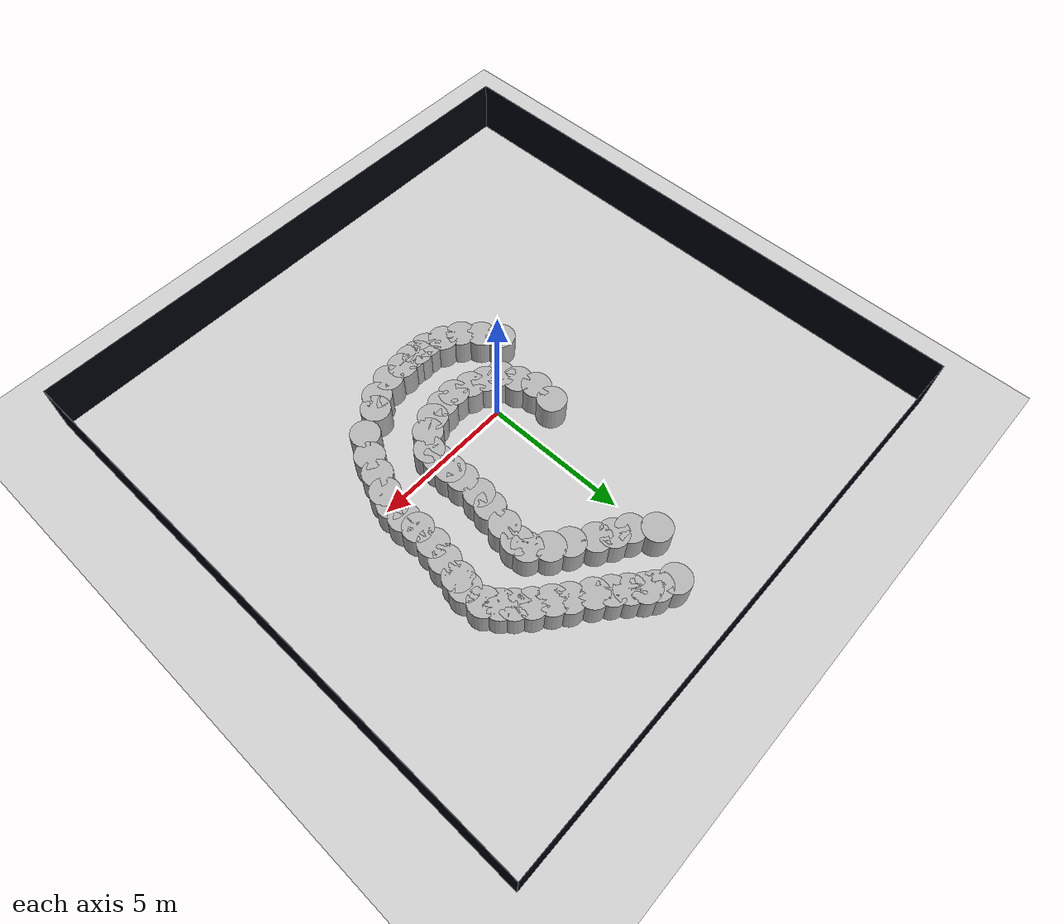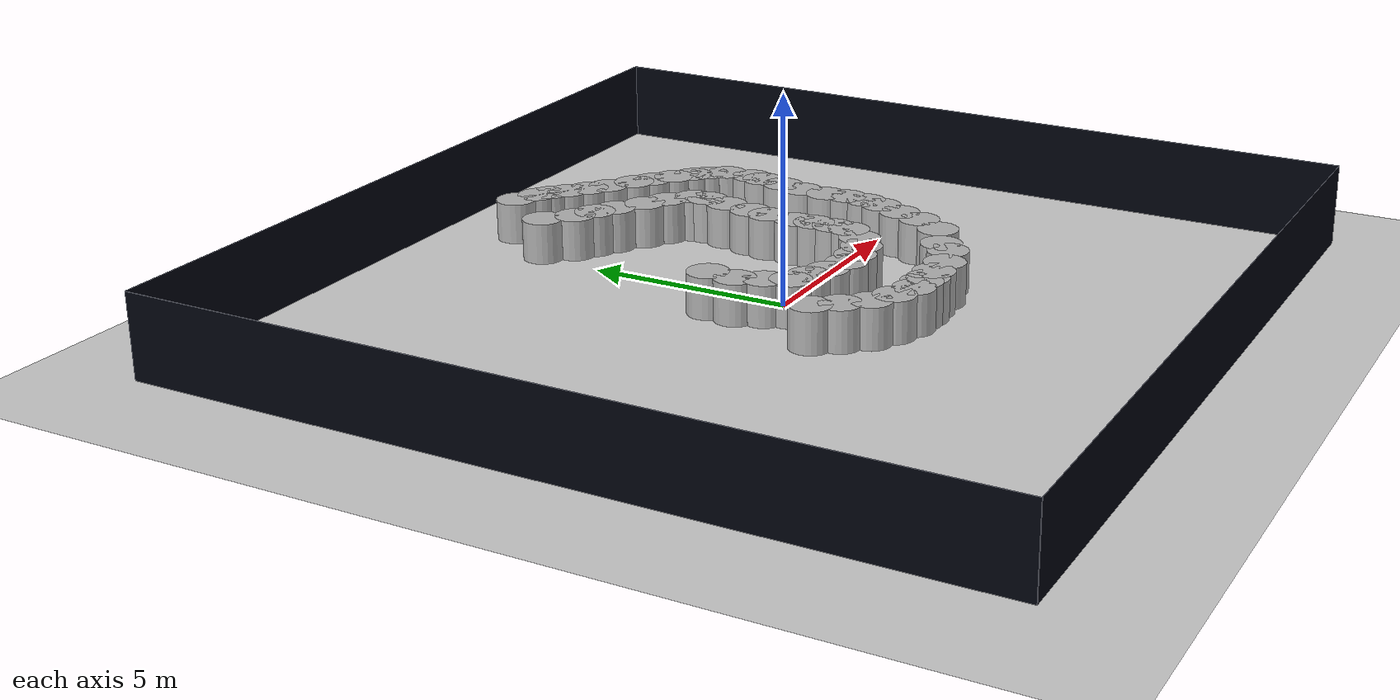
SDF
<sdf version='1.9'>
  <world name='maze'>
    <physics name='1ms' type='ignored'>
      <max_step_size>0.0030000000000000001</max_step_size>
      <real_time_factor>1</real_time_factor>
      <real_time_update_rate>1000</real_time_update_rate>
    </physics>
    <plugin name='ignition::gazebo::systems::Physics' filename='ignition-gazebo-physics-system'/>
    <plugin name='ignition::gazebo::systems::UserCommands' filename='ignition-gazebo-user-commands-system'/>
    <plugin name='ignition::gazebo::systems::SceneBroadcaster' filename='ignition-gazebo-scene-broadcaster-system'/>
    <plugin name='ignition::gazebo::systems::Contact' filename='ignition-gazebo-contact-system'/>
    <gravity>0 0 -9.8</gravity>
    <magnetic_field>6e-06 2.3e-05 -4.2e-05</magnetic_field>
    <atmosphere type='adiabatic'/>
    <scene>
      <ambient>0.4 0.4 0.4 1</ambient>
      <background>0.7 0.7 0.7 1</background>
      <shadows>true</shadows>
    </scene>
    <model name='ground_plane'>
      <static>true</static>
      <link name='link'>
        <collision name='collision'>
          <geometry>
            <plane>
              <normal>0 0 1</normal>
              <size>100 100</size>
            </plane>
          </geometry>
          <surface>
            <friction>
              <ode/>
            </friction>
            <bounce/>
            <contact/>
          </surface>
        </collision>
        <visual name='visual'>
          <geometry>
            <plane>
              <normal>0 0 1</normal>
              <size>100 100</size>
            </plane>
          </geometry>
          <material>
            <ambient>0.8 0.8 0.8 1</ambient>
            <diffuse>0.8 0.8 0.8 1</diffuse>
            <specular>0.8 0.8 0.8 1</specular>
          </material>
          <plugin name='__default__' filename='__default__'/>
        </visual>
        <pose>0 0 0 0 -0 0</pose>
        <inertial>
          <pose>0 0 0 0 -0 0</pose>
          <mass>1</mass>
          <inertia>
            <ixx>1</ixx>
            <ixy>0</ixy>
            <ixz>0</ixz>
            <iyy>1</iyy>
            <iyz>0</iyz>
            <izz>1</izz>
          </inertia>
        </inertial>
        <enable_wind>false</enable_wind>
      </link>
      <plugin name='__default__' filename='__default__'/>
      <pose>0 0 0 0 -0 0</pose>
      <self_collide>false</self_collide>
    </model>
    <model name='border'>
      <pose>0 0 1 0 -0 0</pose>
      <static>true</static>
      <link name='wall1'>
        <pose>-10.005 0 0 0 -0 0</pose>
        <collision name='wall1_collision'>
          <geometry>
            <box>
              <size>0.01 20 2</size>
            </box>
          </geometry>
          <surface>
            <friction>
              <ode/>
            </friction>
            <bounce/>
            <contact/>
          </surface>
        </collision>
        <visual name='wall1_visual'>
          <geometry>
            <box>
              <size>0.01 20 2</size>
            </box>
          </geometry>
          <material>
            <ambient>0.1 0.1 0.1 1</ambient>
            <diffuse>0 0.01 0.05 1</diffuse>
            <specular>0 0.01 0.05 1</specular>
          </material>
        </visual>
        <static>true</static>
        <inertial>
          <pose>0 0 0 0 -0 0</pose>
          <mass>1</mass>
          <inertia>
            <ixx>1</ixx>
            <ixy>0</ixy>
            <ixz>0</ixz>
            <iyy>1</iyy>
            <iyz>0</iyz>
            <izz>1</izz>
          </inertia>
        </inertial>
        <enable_wind>false</enable_wind>
      </link>
      <link name='wall2'>
        <pose>10.005 0 0 0 -0 0</pose>
        <collision name='wall2_collision'>
          <geometry>
            <box>
              <size>0.01 20 2</size>
            </box>
          </geometry>
          <surface>
            <friction>
              <ode/>
            </friction>
            <bounce/>
            <contact/>
          </surface>
        </collision>
        <visual name='wall2_visual'>
          <geometry>
            <box>
              <size>0.01 20 2</size>
            </box>
          </geometry>
          <material>
            <ambient>0.1 0.1 0.1 1</ambient>
            <diffuse>0 0.01 0.05 1</diffuse>
            <specular>0 0.01 0.05 1</specular>
          </material>
        </visual>
        <static>true</static>
        <inertial>
          <pose>0 0 0 0 -0 0</pose>
          <mass>1</mass>
          <inertia>
            <ixx>1</ixx>
            <ixy>0</ixy>
            <ixz>0</ixz>
            <iyy>1</iyy>
            <iyz>0</iyz>
            <izz>1</izz>
          </inertia>
        </inertial>
        <enable_wind>false</enable_wind>
      </link>
      <link name='wall3'>
        <pose>0 10.005 0 0 -0 0</pose>
        <collision name='wall3_collision'>
          <geometry>
            <box>
              <size>20 0.01 2</size>
            </box>
          </geometry>
          <surface>
            <friction>
              <ode/>
            </friction>
            <bounce/>
            <contact/>
          </surface>
        </collision>
        <visual name='wall3_visual'>
          <geometry>
            <box>
              <size>20 0.01 2</size>
            </box>
          </geometry>
          <material>
            <ambient>0.1 0.1 0.1 1</ambient>
            <diffuse>0 0.01 0.05 1</diffuse>
            <specular>0 0.01 0.05 1</specular>
          </material>
        </visual>
        <static>true</static>
        <inertial>
          <pose>0 0 0 0 -0 0</pose>
          <mass>1</mass>
          <inertia>
            <ixx>1</ixx>
            <ixy>0</ixy>
            <ixz>0</ixz>
            <iyy>1</iyy>
            <iyz>0</iyz>
            <izz>1</izz>
          </inertia>
        </inertial>
        <enable_wind>false</enable_wind>
      </link>
      <link name='wall4'>
        <pose>0 -10.005 0 0 -0 0</pose>
        <collision name='wall4_collision'>
          <geometry>
            <box>
              <size>20 0.01 2</size>
            </box>
          </geometry>
          <material>
            <ambient>0.1 0.1 0.1 1</ambient>
            <diffuse>0 0.01 0.05 1</diffuse>
            <specular>0 0.01 0.05 1</specular>
          </material>
          <surface>
            <friction>
              <ode/>
            </friction>
            <bounce/>
            <contact/>
          </surface>
        </collision>
        <visual name='wall4_visual'>
          <geometry>
            <box>
              <size>20 0.01 2</size>
            </box>
          </geometry>
          <material>
            <ambient>0.1 0.1 0.1 1</ambient>
            <diffuse>0 0.01 0.05 1</diffuse>
            <specular>0 0.01 0.05 1</specular>
          </material>
        </visual>
        <static>true</static>
        <inertial>
          <pose>0 0 0 0 -0 0</pose>
          <mass>1</mass>
          <inertia>
            <ixx>1</ixx>
            <ixy>0</ixy>
            <ixz>0</ixz>
            <iyy>1</iyy>
            <iyz>0</iyz>
            <izz>1</izz>
          </inertia>
        </inertial>
        <enable_wind>false</enable_wind>
      </link>
      <self_collide>false</self_collide>
    </model>
    <model name='cylinder_0'>
      <pose>3.00521 -2.5561 0.5 0 -0 0</pose>
      <link name='cylinder_link'>
        <inertial>
          <inertia>
            <ixx>0.14580000000000001</ixx>
            <ixy>0</ixy>
            <ixz>0</ixz>
            <iyy>0.14580000000000001</iyy>
            <iyz>0</iyz>
            <izz>0.125</izz>
          </inertia>
          <mass>1</mass>
          <pose>0 0 0 0 -0 0</pose>
        </inertial>
        <collision name='cylinder_collision'>
          <geometry>
            <cylinder>
              <radius>0.5</radius>
              <length>1</length>
            </cylinder>
          </geometry>
          <surface>
            <friction>
              <ode/>
            </friction>
            <bounce/>
            <contact/>
          </surface>
        </collision>
        <visual name='cylinder_visual'>
          <geometry>
            <cylinder>
              <radius>0.5</radius>
              <length>1</length>
            </cylinder>
          </geometry>
          <material>
            <ambient>0.3 0.3 0.3 1</ambient>
            <diffuse>0.7 0.7 0.7 1</diffuse>
            <specular>1 1 1 1</specular>
          </material>
        </visual>
        <pose>0 0 0 0 -0 0</pose>
        <enable_wind>false</enable_wind>
      </link>
      <static>false</static>
      <self_collide>false</self_collide>
    </model>
    <model name='cylinder_1'>
      <pose>3.87354 -2.0961 0.5 0 -0 0</pose>
      <link name='cylinder_link'>
        <inertial>
          <inertia>
            <ixx>0.14580000000000001</ixx>
            <ixy>0</ixy>
            <ixz>0</ixz>
            <iyy>0.14580000000000001</iyy>
            <iyz>0</iyz>
            <izz>0.125</izz>
          </inertia>
          <mass>1</mass>
        </inertial>
        <collision name='cylinder_collision'>
          <geometry>
            <cylinder>
              <radius>0.5</radius>
              <length>1</length>
            </cylinder>
          </geometry>
          <surface>
            <friction>
              <ode/>
            </friction>
            <bounce/>
            <contact/>
          </surface>
        </collision>
        <visual name='cylinder_visual'>
          <geometry>
            <cylinder>
              <radius>0.5</radius>
              <length>1</length>
            </cylinder>
          </geometry>
          <material>
            <ambient>0.3 0.3 0.3 1</ambient>
            <diffuse>0.7 0.7 0.7 1</diffuse>
            <specular>1 1 1 1</specular>
          </material>
        </visual>
      </link>
      <static>false</static>
      <self_collide>false</self_collide>
    </model>
    <model name='cylinder_2'>
      <pose>4.32003 -1.40842 0.5 0 -0 0</pose>
      <link name='cylinder_link'>
        <inertial>
          <inertia>
            <ixx>0.14580000000000001</ixx>
            <ixy>0</ixy>
            <ixz>0</ixz>
            <iyy>0.14580000000000001</iyy>
            <iyz>0</iyz>
            <izz>0.125</izz>
          </inertia>
          <mass>1</mass>
        </inertial>
        <collision name='cylinder_collision'>
          <geometry>
            <cylinder>
              <radius>0.5</radius>
              <length>1</length>
            </cylinder>
          </geometry>
          <surface>
            <friction>
              <ode/>
            </friction>
            <bounce/>
            <contact/>
          </surface>
        </collision>
        <visual name='cylinder_visual'>
          <geometry>
            <cylinder>
              <radius>0.5</radius>
              <length>1</length>
            </cylinder>
          </geometry>
          <material>
            <ambient>0.3 0.3 0.3 1</ambient>
            <diffuse>0.7 0.7 0.7 1</diffuse>
            <specular>1 1 1 1</specular>
          </material>
        </visual>
      </link>
      <static>false</static>
      <self_collide>false</self_collide>
    </model>
    <model name='cylinder_3'>
      <pose>4.57445 -0.779737 0.5 0 -0 0</pose>
      <link name='cylinder_link'>
        <inertial>
          <inertia>
            <ixx>0.14580000000000001</ixx>
            <ixy>0</ixy>
            <ixz>0</ixz>
            <iyy>0.14580000000000001</iyy>
            <iyz>0</iyz>
            <izz>0.125</izz>
          </inertia>
          <mass>1</mass>
        </inertial>
        <collision name='cylinder_collision'>
          <geometry>
            <cylinder>
              <radius>0.5</radius>
              <length>1</length>
            </cylinder>
          </geometry>
          <surface>
            <friction>
              <ode/>
            </friction>
            <bounce/>
            <contact/>
          </surface>
        </collision>
        <visual name='cylinder_visual'>
          <geometry>
            <cylinder>
              <radius>0.5</radius>
              <length>1</length>
            </cylinder>
          </geometry>
          <material>
            <ambient>0.3 0.3 0.3 1</ambient>
            <diffuse>0.7 0.7 0.7 1</diffuse>
            <specular>1 1 1 1</specular>
          </material>
        </visual>
      </link>
      <static>false</static>
      <self_collide>false</self_collide>
    </model>
    <model name='cylinder_4'>
      <pose>4.8528 -0.143647 0.5 0 -0 0</pose>
      <link name='cylinder_link'>
        <inertial>
          <inertia>
            <ixx>0.14580000000000001</ixx>
            <ixy>0</ixy>
            <ixz>0</ixz>
            <iyy>0.14580000000000001</iyy>
            <iyz>0</iyz>
            <izz>0.125</izz>
          </inertia>
          <mass>1</mass>
        </inertial>
        <collision name='cylinder_collision'>
          <geometry>
            <cylinder>
              <radius>0.5</radius>
              <length>1</length>
            </cylinder>
          </geometry>
          <surface>
            <friction>
              <ode/>
            </friction>
            <bounce/>
            <contact/>
          </surface>
        </collision>
        <visual name='cylinder_visual'>
          <geometry>
            <cylinder>
              <radius>0.5</radius>
              <length>1</length>
            </cylinder>
          </geometry>
          <material>
            <ambient>0.3 0.3 0.3 1</ambient>
            <diffuse>0.7 0.7 0.7 1</diffuse>
            <specular>1 1 1 1</specular>
          </material>
        </visual>
      </link>
      <static>false</static>
      <self_collide>false</self_collide>
    </model>
    <model name='cylinder_5'>
      <pose>5.00234 0.347947 0.5 0 -0 0</pose>
      <link name='cylinder_link'>
        <inertial>
          <inertia>
            <ixx>0.14580000000000001</ixx>
            <ixy>0</ixy>
            <ixz>0</ixz>
            <iyy>0.14580000000000001</iyy>
            <iyz>0</iyz>
            <izz>0.125</izz>
          </inertia>
          <mass>1</mass>
        </inertial>
        <collision name='cylinder_collision'>
          <geometry>
            <cylinder>
              <radius>0.5</radius>
              <length>1</length>
            </cylinder>
          </geometry>
          <surface>
            <friction>
              <ode/>
            </friction>
            <bounce/>
            <contact/>
          </surface>
        </collision>
        <visual name='cylinder_visual'>
          <geometry>
            <cylinder>
              <radius>0.5</radius>
              <length>1</length>
            </cylinder>
          </geometry>
          <material>
            <ambient>0.3 0.3 0.3 1</ambient>
            <diffuse>0.7 0.7 0.7 1</diffuse>
            <specular>1 1 1 1</specular>
          </material>
        </visual>
      </link>
      <static>false</static>
      <self_collide>false</self_collide>
    </model>
    <model name='cylinder_6'>
      <pose>5.05596 0.90192 0.5 0 -0 0</pose>
      <link name='cylinder_link'>
        <inertial>
          <inertia>
            <ixx>0.14580000000000001</ixx>
            <ixy>0</ixy>
            <ixz>0</ixz>
            <iyy>0.14580000000000001</iyy>
            <iyz>0</iyz>
            <izz>0.125</izz>
          </inertia>
          <mass>1</mass>
        </inertial>
        <collision name='cylinder_collision'>
          <geometry>
            <cylinder>
              <radius>0.5</radius>
              <length>1</length>
            </cylinder>
          </geometry>
          <surface>
            <friction>
              <ode/>
            </friction>
            <bounce/>
            <contact/>
          </surface>
        </collision>
        <visual name='cylinder_visual'>
          <geometry>
            <cylinder>
              <radius>0.5</radius>
              <length>1</length>
            </cylinder>
          </geometry>
          <material>
            <ambient>0.3 0.3 0.3 1</ambient>
            <diffuse>0.7 0.7 0.7 1</diffuse>
            <specular>1 1 1 1</specular>
          </material>
        </visual>
      </link>
      <static>false</static>
      <self_collide>false</self_collide>
    </model>
    <model name='cylinder_7'>
      <pose>5.00665 1.43891 0.5 0 -0 0</pose>
      <link name='cylinder_link'>
        <inertial>
          <inertia>
            <ixx>0.14580000000000001</ixx>
            <ixy>0</ixy>
            <ixz>0</ixz>
            <iyy>0.14580000000000001</iyy>
            <iyz>0</iyz>
            <izz>0.125</izz>
          </inertia>
          <mass>1</mass>
        </inertial>
        <collision name='cylinder_collision'>
          <geometry>
            <cylinder>
              <radius>0.5</radius>
              <length>1</length>
            </cylinder>
          </geometry>
          <surface>
            <friction>
              <ode/>
            </friction>
            <bounce/>
            <contact/>
          </surface>
        </collision>
        <visual name='cylinder_visual'>
          <geometry>
            <cylinder>
              <radius>0.5</radius>
              <length>1</length>
            </cylinder>
          </geometry>
          <material>
            <ambient>0.3 0.3 0.3 1</ambient>
            <diffuse>0.7 0.7 0.7 1</diffuse>
            <specular>1 1 1 1</specular>
          </material>
        </visual>
      </link>
      <static>false</static>
      <self_collide>false</self_collide>
    </model>
    <model name='cylinder_8'>
      <pose>1.9737 -0.993589 0.5 0 -0 0</pose>
      <link name='cylinder_link'>
        <inertial>
          <inertia>
            <ixx>0.14580000000000001</ixx>
            <ixy>0</ixy>
            <ixz>0</ixz>
            <iyy>0.14580000000000001</iyy>
            <iyz>0</iyz>
            <izz>0.125</izz>
          </inertia>
          <mass>1</mass>
        </inertial>
        <collision name='cylinder_collision'>
          <geometry>
            <cylinder>
              <radius>0.5</radius>
              <length>1</length>
            </cylinder>
          </geometry>
          <surface>
            <friction>
              <ode/>
            </friction>
            <bounce/>
            <contact/>
          </surface>
        </collision>
        <visual name='cylinder_visual'>
          <geometry>
            <cylinder>
              <radius>0.5</radius>
              <length>1</length>
            </cylinder>
          </geometry>
          <material>
            <ambient>0.3 0.3 0.3 1</ambient>
            <diffuse>0.7 0.7 0.7 1</diffuse>
            <specular>1 1 1 1</specular>
          </material>
        </visual>
      </link>
      <static>false</static>
      <self_collide>false</self_collide>
    </model>
    <model name='cylinder_9'>
      <pose>2.46111 -0.714718 0.5 0 -0 0</pose>
      <link name='cylinder_link'>
        <inertial>
          <inertia>
            <ixx>0.14580000000000001</ixx>
            <ixy>0</ixy>
            <ixz>0</ixz>
            <iyy>0.14580000000000001</iyy>
            <iyz>0</iyz>
            <izz>0.125</izz>
          </inertia>
          <mass>1</mass>
        </inertial>
        <collision name='cylinder_collision'>
          <geometry>
            <cylinder>
              <radius>0.5</radius>
              <length>1</length>
            </cylinder>
          </geometry>
          <surface>
            <friction>
              <ode/>
            </friction>
            <bounce/>
            <contact/>
          </surface>
        </collision>
        <visual name='cylinder_visual'>
          <geometry>
            <cylinder>
              <radius>0.5</radius>
              <length>1</length>
            </cylinder>
          </geometry>
          <material>
            <ambient>0.3 0.3 0.3 1</ambient>
            <diffuse>0.7 0.7 0.7 1</diffuse>
            <specular>1 1 1 1</specular>
          </material>
        </visual>
      </link>
      <static>false</static>
      <self_collide>false</self_collide>
    </model>
    <model name='cylinder_10'>
      <pose>2.89554 -0.219933 0.5 0 -0 0</pose>
      <link name='cylinder_link'>
        <inertial>
          <inertia>
            <ixx>0.14580000000000001</ixx>
            <ixy>0</ixy>
            <ixz>0</ixz>
            <iyy>0.14580000000000001</iyy>
            <iyz>0</iyz>
            <izz>0.125</izz>
          </inertia>
          <mass>1</mass>
        </inertial>
        <collision name='cylinder_collision'>
          <geometry>
            <cylinder>
              <radius>0.5</radius>
              <length>1</length>
            </cylinder>
          </geometry>
          <surface>
            <friction>
              <ode/>
            </friction>
            <bounce/>
            <contact/>
          </surface>
        </collision>
        <visual name='cylinder_visual'>
          <geometry>
            <cylinder>
              <radius>0.5</radius>
              <length>1</length>
            </cylinder>
          </geometry>
          <material>
            <ambient>0.3 0.3 0.3 1</ambient>
            <diffuse>0.7 0.7 0.7 1</diffuse>
            <specular>1 1 1 1</specular>
          </material>
        </visual>
      </link>
      <static>false</static>
      <self_collide>false</self_collide>
    </model>
    <model name='cylinder_11'>
      <pose>2.93304 0.219179 0.5 0 -0 0</pose>
      <link name='cylinder_link'>
        <inertial>
          <inertia>
            <ixx>0.14580000000000001</ixx>
            <ixy>0</ixy>
            <ixz>0</ixz>
            <iyy>0.14580000000000001</iyy>
            <iyz>0</iyz>
            <izz>0.125</izz>
          </inertia>
          <mass>1</mass>
        </inertial>
        <collision name='cylinder_collision'>
          <geometry>
            <cylinder>
              <radius>0.5</radius>
              <length>1</length>
            </cylinder>
          </geometry>
          <surface>
            <friction>
              <ode/>
            </friction>
            <bounce/>
            <contact/>
          </surface>
        </collision>
        <visual name='cylinder_visual'>
          <geometry>
            <cylinder>
              <radius>0.5</radius>
              <length>1</length>
            </cylinder>
          </geometry>
          <material>
            <ambient>0.3 0.3 0.3 1</ambient>
            <diffuse>0.7 0.7 0.7 1</diffuse>
            <specular>1 1 1 1</specular>
          </material>
        </visual>
      </link>
      <static>false</static>
      <self_collide>false</self_collide>
    </model>
    <model name='cylinder_12'>
      <pose>2.94015 0.728418 0.5 0 -0 0</pose>
      <link name='cylinder_link'>
        <inertial>
          <inertia>
            <ixx>0.14580000000000001</ixx>
            <ixy>0</ixy>
            <ixz>0</ixz>
            <iyy>0.14580000000000001</iyy>
            <iyz>0</iyz>
            <izz>0.125</izz>
          </inertia>
          <mass>1</mass>
        </inertial>
        <collision name='cylinder_collision'>
          <geometry>
            <cylinder>
              <radius>0.5</radius>
              <length>1</length>
            </cylinder>
          </geometry>
          <surface>
            <friction>
              <ode/>
            </friction>
            <bounce/>
            <contact/>
          </surface>
        </collision>
        <visual name='cylinder_visual'>
          <geometry>
            <cylinder>
              <radius>0.5</radius>
              <length>1</length>
            </cylinder>
          </geometry>
          <material>
            <ambient>0.3 0.3 0.3 1</ambient>
            <diffuse>0.7 0.7 0.7 1</diffuse>
            <specular>1 1 1 1</specular>
          </material>
        </visual>
      </link>
      <static>false</static>
      <self_collide>false</self_collide>
    </model>
    <model name='cylinder_13'>
      <pose>2.89583 1.22956 0.5 0 -0 0</pose>
      <link name='cylinder_link'>
        <inertial>
          <inertia>
            <ixx>0.14580000000000001</ixx>
            <ixy>0</ixy>
            <ixz>0</ixz>
            <iyy>0.14580000000000001</iyy>
            <iyz>0</iyz>
            <izz>0.125</izz>
          </inertia>
          <mass>1</mass>
        </inertial>
        <collision name='cylinder_collision'>
          <geometry>
            <cylinder>
              <radius>0.5</radius>
              <length>1</length>
            </cylinder>
          </geometry>
          <surface>
            <friction>
              <ode/>
            </friction>
            <bounce/>
            <contact/>
          </surface>
        </collision>
        <visual name='cylinder_visual'>
          <geometry>
            <cylinder>
              <radius>0.5</radius>
              <length>1</length>
            </cylinder>
          </geometry>
          <material>
            <ambient>0.3 0.3 0.3 1</ambient>
            <diffuse>0.7 0.7 0.7 1</diffuse>
            <specular>1 1 1 1</specular>
          </material>
        </visual>
      </link>
      <static>false</static>
      <self_collide>false</self_collide>
    </model>
    <model name='cylinder_14'>
      <pose>2.93199 1.96354 0.5 0 -0 0</pose>
      <link name='cylinder_link'>
        <inertial>
          <inertia>
            <ixx>0.14580000000000001</ixx>
            <ixy>0</ixy>
            <ixz>0</ixz>
            <iyy>0.14580000000000001</iyy>
            <iyz>0</iyz>
            <izz>0.125</izz>
          </inertia>
          <mass>1</mass>
        </inertial>
        <collision name='cylinder_collision'>
          <geometry>
            <cylinder>
              <radius>0.5</radius>
              <length>1</length>
            </cylinder>
          </geometry>
          <surface>
            <friction>
              <ode/>
            </friction>
            <bounce/>
            <contact/>
          </surface>
        </collision>
        <visual name='cylinder_visual'>
          <geometry>
            <cylinder>
              <radius>0.5</radius>
              <length>1</length>
            </cylinder>
          </geometry>
          <material>
            <ambient>0.3 0.3 0.3 1</ambient>
            <diffuse>0.7 0.7 0.7 1</diffuse>
            <specular>1 1 1 1</specular>
          </material>
        </visual>
      </link>
      <static>false</static>
      <self_collide>false</self_collide>
    </model>
    <model name='cylinder_15'>
      <pose>3.02494 2.50982 0.5 0 -0 0</pose>
      <link name='cylinder_link'>
        <inertial>
          <inertia>
            <ixx>0.14580000000000001</ixx>
            <ixy>0</ixy>
            <ixz>0</ixz>
            <iyy>0.14580000000000001</iyy>
            <iyz>0</iyz>
            <izz>0.125</izz>
          </inertia>
          <mass>1</mass>
        </inertial>
        <collision name='cylinder_collision'>
          <geometry>
            <cylinder>
              <radius>0.5</radius>
              <length>1</length>
            </cylinder>
          </geometry>
          <surface>
            <friction>
              <ode/>
            </friction>
            <bounce/>
            <contact/>
          </surface>
        </collision>
        <visual name='cylinder_visual'>
          <geometry>
            <cylinder>
              <radius>0.5</radius>
              <length>1</length>
            </cylinder>
          </geometry>
          <material>
            <ambient>0.3 0.3 0.3 1</ambient>
            <diffuse>0.7 0.7 0.7 1</diffuse>
            <specular>1 1 1 1</specular>
          </material>
        </visual>
      </link>
      <static>false</static>
      <self_collide>false</self_collide>
    </model>
    <model name='cylinder_16'>
      <pose>5.04031 2.12177 0.5 0 -0 0</pose>
      <link name='cylinder_link'>
        <inertial>
          <inertia>
            <ixx>0.14580000000000001</ixx>
            <ixy>0</ixy>
            <ixz>0</ixz>
            <iyy>0.14580000000000001</iyy>
            <iyz>0</iyz>
            <izz>0.125</izz>
          </inertia>
          <mass>1</mass>
        </inertial>
        <collision name='cylinder_collision'>
          <geometry>
            <cylinder>
              <radius>0.5</radius>
              <length>1</length>
            </cylinder>
          </geometry>
          <surface>
            <friction>
              <ode/>
            </friction>
            <bounce/>
            <contact/>
          </surface>
        </collision>
        <visual name='cylinder_visual'>
          <geometry>
            <cylinder>
              <radius>0.5</radius>
              <length>1</length>
            </cylinder>
          </geometry>
          <material>
            <ambient>0.3 0.3 0.3 1</ambient>
            <diffuse>0.7 0.7 0.7 1</diffuse>
            <specular>1 1 1 1</specular>
          </material>
        </visual>
      </link>
      <static>false</static>
      <self_collide>false</self_collide>
    </model>
    <model name='cylinder_17'>
      <pose>3.17881 3.24577 0.5 0 -0 0</pose>
      <link name='cylinder_link'>
        <inertial>
          <inertia>
            <ixx>0.14580000000000001</ixx>
            <ixy>0</ixy>
            <ixz>0</ixz>
            <iyy>0.14580000000000001</iyy>
            <iyz>0</iyz>
            <izz>0.125</izz>
          </inertia>
          <mass>1</mass>
        </inertial>
        <collision name='cylinder_collision'>
          <geometry>
            <cylinder>
              <radius>0.5</radius>
              <length>1</length>
            </cylinder>
          </geometry>
          <surface>
            <friction>
              <ode/>
            </friction>
            <bounce/>
            <contact/>
          </surface>
        </collision>
        <visual name='cylinder_visual'>
          <geometry>
            <cylinder>
              <radius>0.5</radius>
              <length>1</length>
            </cylinder>
          </geometry>
          <material>
            <ambient>0.3 0.3 0.3 1</ambient>
            <diffuse>0.7 0.7 0.7 1</diffuse>
            <specular>1 1 1 1</specular>
          </material>
        </visual>
      </link>
      <static>false</static>
      <self_collide>false</self_collide>
    </model>
    <model name='cylinder_18'>
      <pose>3.30953 3.86336 0.5 0 -0 0</pose>
      <link name='cylinder_link'>
        <inertial>
          <inertia>
            <ixx>0.14580000000000001</ixx>
            <ixy>0</ixy>
            <ixz>0</ixz>
            <iyy>0.14580000000000001</iyy>
            <iyz>0</iyz>
            <izz>0.125</izz>
          </inertia>
          <mass>1</mass>
        </inertial>
        <collision name='cylinder_collision'>
          <geometry>
            <cylinder>
              <radius>0.5</radius>
              <length>1</length>
            </cylinder>
          </geometry>
          <surface>
            <friction>
              <ode/>
            </friction>
            <bounce/>
            <contact/>
          </surface>
        </collision>
        <visual name='cylinder_visual'>
          <geometry>
            <cylinder>
              <radius>0.5</radius>
              <length>1</length>
            </cylinder>
          </geometry>
          <material>
            <ambient>0.3 0.3 0.3 1</ambient>
            <diffuse>0.7 0.7 0.7 1</diffuse>
            <specular>1 1 1 1</specular>
          </material>
        </visual>
      </link>
      <static>false</static>
      <self_collide>false</self_collide>
    </model>
    <model name='cylinder_19'>
      <pose>3.26516 4.22192 0.5 0 -0 0</pose>
      <link name='cylinder_link'>
        <inertial>
          <inertia>
            <ixx>0.14580000000000001</ixx>
            <ixy>0</ixy>
            <ixz>0</ixz>
            <iyy>0.14580000000000001</iyy>
            <iyz>0</iyz>
            <izz>0.125</izz>
          </inertia>
          <mass>1</mass>
        </inertial>
        <collision name='cylinder_collision'>
          <geometry>
            <cylinder>
              <radius>0.5</radius>
              <length>1</length>
            </cylinder>
          </geometry>
          <surface>
            <friction>
              <ode/>
            </friction>
            <bounce/>
            <contact/>
          </surface>
        </collision>
        <visual name='cylinder_visual'>
          <geometry>
            <cylinder>
              <radius>0.5</radius>
              <length>1</length>
            </cylinder>
          </geometry>
          <material>
            <ambient>0.3 0.3 0.3 1</ambient>
            <diffuse>0.7 0.7 0.7 1</diffuse>
            <specular>1 1 1 1</specular>
          </material>
        </visual>
      </link>
      <static>false</static>
      <self_collide>false</self_collide>
    </model>
    <model name='cylinder_20'>
      <pose>2.79599 4.70402 0.5 0 -0 0</pose>
      <link name='cylinder_link'>
        <inertial>
          <inertia>
            <ixx>0.14580000000000001</ixx>
            <ixy>0</ixy>
            <ixz>0</ixz>
            <iyy>0.14580000000000001</iyy>
            <iyz>0</iyz>
            <izz>0.125</izz>
          </inertia>
          <mass>1</mass>
        </inertial>
        <collision name='cylinder_collision'>
          <geometry>
            <cylinder>
              <radius>0.5</radius>
              <length>1</length>
            </cylinder>
          </geometry>
          <surface>
            <friction>
              <ode/>
            </friction>
            <bounce/>
            <contact/>
          </surface>
        </collision>
        <visual name='cylinder_visual'>
          <geometry>
            <cylinder>
              <radius>0.5</radius>
              <length>1</length>
            </cylinder>
          </geometry>
          <material>
            <ambient>0.3 0.3 0.3 1</ambient>
            <diffuse>0.7 0.7 0.7 1</diffuse>
            <specular>1 1 1 1</specular>
          </material>
        </visual>
      </link>
      <static>false</static>
      <self_collide>false</self_collide>
    </model>
    <model name='cylinder_21'>
      <pose>2.27964 5.04206 0.5 0 -0 0</pose>
      <link name='cylinder_link'>
        <inertial>
          <inertia>
            <ixx>0.14580000000000001</ixx>
            <ixy>0</ixy>
            <ixz>0</ixz>
            <iyy>0.14580000000000001</iyy>
            <iyz>0</iyz>
            <izz>0.125</izz>
          </inertia>
          <mass>1</mass>
        </inertial>
        <collision name='cylinder_collision'>
          <geometry>
            <cylinder>
              <radius>0.5</radius>
              <length>1</length>
            </cylinder>
          </geometry>
          <surface>
            <friction>
              <ode/>
            </friction>
            <bounce/>
            <contact/>
          </surface>
        </collision>
        <visual name='cylinder_visual'>
          <geometry>
            <cylinder>
              <radius>0.5</radius>
              <length>1</length>
            </cylinder>
          </geometry>
          <material>
            <ambient>0.3 0.3 0.3 1</ambient>
            <diffuse>0.7 0.7 0.7 1</diffuse>
            <specular>1 1 1 1</specular>
          </material>
        </visual>
      </link>
      <static>false</static>
      <self_collide>false</self_collide>
    </model>
    <model name='cylinder_22'>
      <pose>1.64436 5.50225 0.5 0 -0 0</pose>
      <link name='cylinder_link'>
        <inertial>
          <inertia>
            <ixx>0.14580000000000001</ixx>
            <ixy>0</ixy>
            <ixz>0</ixz>
            <iyy>0.14580000000000001</iyy>
            <iyz>0</iyz>
            <izz>0.125</izz>
          </inertia>
          <mass>1</mass>
        </inertial>
        <collision name='cylinder_collision'>
          <geometry>
            <cylinder>
              <radius>0.5</radius>
              <length>1</length>
            </cylinder>
          </geometry>
          <surface>
            <friction>
              <ode/>
            </friction>
            <bounce/>
            <contact/>
          </surface>
        </collision>
        <visual name='cylinder_visual'>
          <geometry>
            <cylinder>
              <radius>0.5</radius>
              <length>1</length>
            </cylinder>
          </geometry>
          <material>
            <ambient>0.3 0.3 0.3 1</ambient>
            <diffuse>0.7 0.7 0.7 1</diffuse>
            <specular>1 1 1 1</specular>
          </material>
        </visual>
      </link>
      <static>false</static>
      <self_collide>false</self_collide>
    </model>
    <model name='cylinder_23'>
      <pose>0.716786 6.0641 0.5 0 -0 0</pose>
      <link name='cylinder_link'>
        <inertial>
          <inertia>
            <ixx>0.14580000000000001</ixx>
            <ixy>0</ixy>
            <ixz>0</ixz>
            <iyy>0.14580000000000001</iyy>
            <iyz>0</iyz>
            <izz>0.125</izz>
          </inertia>
          <mass>1</mass>
        </inertial>
        <collision name='cylinder_collision'>
          <geometry>
            <cylinder>
              <radius>0.5</radius>
              <length>1</length>
            </cylinder>
          </geometry>
          <surface>
            <friction>
              <ode/>
            </friction>
            <bounce/>
            <contact/>
          </surface>
        </collision>
        <visual name='cylinder_visual'>
          <geometry>
            <cylinder>
              <radius>0.5</radius>
              <length>1</length>
            </cylinder>
          </geometry>
          <material>
            <ambient>0.3 0.3 0.3 1</ambient>
            <diffuse>0.7 0.7 0.7 1</diffuse>
            <specular>1 1 1 1</specular>
          </material>
        </visual>
      </link>
      <static>false</static>
      <self_collide>false</self_collide>
    </model>
    <model name='cylinder_24'>
      <pose>1.1856 5.79695 0.5 0 -0 0</pose>
      <link name='cylinder_link'>
        <inertial>
          <inertia>
            <ixx>0.14580000000000001</ixx>
            <ixy>0</ixy>
            <ixz>0</ixz>
            <iyy>0.14580000000000001</iyy>
            <iyz>0</iyz>
            <izz>0.125</izz>
          </inertia>
          <mass>1</mass>
        </inertial>
        <collision name='cylinder_collision'>
          <geometry>
            <cylinder>
              <radius>0.5</radius>
              <length>1</length>
            </cylinder>
          </geometry>
          <surface>
            <friction>
              <ode/>
            </friction>
            <bounce/>
            <contact/>
          </surface>
        </collision>
        <visual name='cylinder_visual'>
          <geometry>
            <cylinder>
              <radius>0.5</radius>
              <length>1</length>
            </cylinder>
          </geometry>
          <material>
            <ambient>0.3 0.3 0.3 1</ambient>
            <diffuse>0.7 0.7 0.7 1</diffuse>
            <specular>1 1 1 1</specular>
          </material>
        </visual>
      </link>
      <static>false</static>
      <self_collide>false</self_collide>
    </model>
    <model name='cylinder_25'>
      <pose>0.160367 6.62092 0.5 0 -0 0</pose>
      <link name='cylinder_link'>
        <inertial>
          <inertia>
            <ixx>0.14580000000000001</ixx>
            <ixy>0</ixy>
            <ixz>0</ixz>
            <iyy>0.14580000000000001</iyy>
            <iyz>0</iyz>
            <izz>0.125</izz>
          </inertia>
          <mass>1</mass>
        </inertial>
        <collision name='cylinder_collision'>
          <geometry>
            <cylinder>
              <radius>0.5</radius>
              <length>1</length>
            </cylinder>
          </geometry>
          <surface>
            <friction>
              <ode/>
            </friction>
            <bounce/>
            <contact/>
          </surface>
        </collision>
        <visual name='cylinder_visual'>
          <geometry>
            <cylinder>
              <radius>0.5</radius>
              <length>1</length>
            </cylinder>
          </geometry>
          <material>
            <ambient>0.3 0.3 0.3 1</ambient>
            <diffuse>0.7 0.7 0.7 1</diffuse>
            <specular>1 1 1 1</specular>
          </material>
        </visual>
      </link>
      <static>false</static>
      <self_collide>false</self_collide>
    </model>
    <model name='cylinder_26'>
      <pose>5.17862 2.742 0.5 0 -0 0</pose>
      <link name='cylinder_link'>
        <inertial>
          <inertia>
            <ixx>0.14580000000000001</ixx>
            <ixy>0</ixy>
            <ixz>0</ixz>
            <iyy>0.14580000000000001</iyy>
            <iyz>0</iyz>
            <izz>0.125</izz>
          </inertia>
          <mass>1</mass>
          <pose>0 0 0 0 -0 0</pose>
        </inertial>
        <collision name='cylinder_collision'>
          <geometry>
            <cylinder>
              <radius>0.5</radius>
              <length>1</length>
            </cylinder>
          </geometry>
          <surface>
            <friction>
              <ode/>
            </friction>
            <bounce/>
            <contact/>
          </surface>
        </collision>
        <visual name='cylinder_visual'>
          <geometry>
            <cylinder>
              <radius>0.5</radius>
              <length>1</length>
            </cylinder>
          </geometry>
          <material>
            <ambient>0.3 0.3 0.3 1</ambient>
            <diffuse>0.7 0.7 0.7 1</diffuse>
            <specular>1 1 1 1</specular>
          </material>
        </visual>
        <pose>0 0 0 0 -0 0</pose>
        <enable_wind>false</enable_wind>
      </link>
      <static>false</static>
      <self_collide>false</self_collide>
    </model>
    <model name='cylinder_27'>
      <pose>5.30273 3.39871 0.5 0 -0 0</pose>
      <link name='cylinder_link'>
        <inertial>
          <inertia>
            <ixx>0.14580000000000001</ixx>
            <ixy>0</ixy>
            <ixz>0</ixz>
            <iyy>0.14580000000000001</iyy>
            <iyz>0</iyz>
            <izz>0.125</izz>
          </inertia>
          <mass>1</mass>
        </inertial>
        <collision name='cylinder_collision'>
          <geometry>
            <cylinder>
              <radius>0.5</radius>
              <length>1</length>
            </cylinder>
          </geometry>
          <surface>
            <friction>
              <ode/>
            </friction>
            <bounce/>
            <contact/>
          </surface>
        </collision>
        <visual name='cylinder_visual'>
          <geometry>
            <cylinder>
              <radius>0.5</radius>
              <length>1</length>
            </cylinder>
          </geometry>
          <material>
            <ambient>0.3 0.3 0.3 1</ambient>
            <diffuse>0.7 0.7 0.7 1</diffuse>
            <specular>1 1 1 1</specular>
          </material>
        </visual>
      </link>
      <static>false</static>
      <self_collide>false</self_collide>
    </model>
    <model name='cylinder_28'>
      <pose>5.38687 3.75792 0.5 0 -0 0</pose>
      <link name='cylinder_link'>
        <inertial>
          <inertia>
            <ixx>0.14580000000000001</ixx>
            <ixy>0</ixy>
            <ixz>0</ixz>
            <iyy>0.14580000000000001</iyy>
            <iyz>0</iyz>
            <izz>0.125</izz>
          </inertia>
          <mass>1</mass>
        </inertial>
        <collision name='cylinder_collision'>
          <geometry>
            <cylinder>
              <radius>0.5</radius>
              <length>1</length>
            </cylinder>
          </geometry>
          <surface>
            <friction>
              <ode/>
            </friction>
            <bounce/>
            <contact/>
          </surface>
        </collision>
        <visual name='cylinder_visual'>
          <geometry>
            <cylinder>
              <radius>0.5</radius>
              <length>1</length>
            </cylinder>
          </geometry>
          <material>
            <ambient>0.3 0.3 0.3 1</ambient>
            <diffuse>0.7 0.7 0.7 1</diffuse>
            <specular>1 1 1 1</specular>
          </material>
        </visual>
      </link>
      <static>false</static>
      <self_collide>false</self_collide>
    </model>
    <model name='cylinder_29'>
      <pose>5.35531 4.44847 0.5 0 -0 0</pose>
      <link name='cylinder_link'>
        <inertial>
          <inertia>
            <ixx>0.14580000000000001</ixx>
            <ixy>0</ixy>
            <ixz>0</ixz>
            <iyy>0.14580000000000001</iyy>
            <iyz>0</iyz>
            <izz>0.125</izz>
          </inertia>
          <mass>1</mass>
        </inertial>
        <collision name='cylinder_collision'>
          <geometry>
            <cylinder>
              <radius>0.5</radius>
              <length>1</length>
            </cylinder>
          </geometry>
          <surface>
            <friction>
              <ode/>
            </friction>
            <bounce/>
            <contact/>
          </surface>
        </collision>
        <visual name='cylinder_visual'>
          <geometry>
            <cylinder>
              <radius>0.5</radius>
              <length>1</length>
            </cylinder>
          </geometry>
          <material>
            <ambient>0.3 0.3 0.3 1</ambient>
            <diffuse>0.7 0.7 0.7 1</diffuse>
            <specular>1 1 1 1</specular>
          </material>
        </visual>
      </link>
      <static>false</static>
      <self_collide>false</self_collide>
    </model>
    <model name='cylinder_30'>
      <pose>5.09301 4.84558 0.5 0 -0 0</pose>
      <link name='cylinder_link'>
        <inertial>
          <inertia>
            <ixx>0.14580000000000001</ixx>
            <ixy>0</ixy>
            <ixz>0</ixz>
            <iyy>0.14580000000000001</iyy>
            <iyz>0</iyz>
            <izz>0.125</izz>
          </inertia>
          <mass>1</mass>
        </inertial>
        <collision name='cylinder_collision'>
          <geometry>
            <cylinder>
              <radius>0.5</radius>
              <length>1</length>
            </cylinder>
          </geometry>
          <surface>
            <friction>
              <ode/>
            </friction>
            <bounce/>
            <contact/>
          </surface>
        </collision>
        <visual name='cylinder_visual'>
          <geometry>
            <cylinder>
              <radius>0.5</radius>
              <length>1</length>
            </cylinder>
          </geometry>
          <material>
            <ambient>0.3 0.3 0.3 1</ambient>
            <diffuse>0.7 0.7 0.7 1</diffuse>
            <specular>1 1 1 1</specular>
          </material>
        </visual>
      </link>
      <static>false</static>
      <self_collide>false</self_collide>
    </model>
    <model name='cylinder_31'>
      <pose>4.81726 5.14263 0.5 0 -0 0</pose>
      <link name='cylinder_link'>
        <inertial>
          <inertia>
            <ixx>0.14580000000000001</ixx>
            <ixy>0</ixy>
            <ixz>0</ixz>
            <iyy>0.14580000000000001</iyy>
            <iyz>0</iyz>
            <izz>0.125</izz>
          </inertia>
          <mass>1</mass>
        </inertial>
        <collision name='cylinder_collision'>
          <geometry>
            <cylinder>
              <radius>0.5</radius>
              <length>1</length>
            </cylinder>
          </geometry>
          <surface>
            <friction>
              <ode/>
            </friction>
            <bounce/>
            <contact/>
          </surface>
        </collision>
        <visual name='cylinder_visual'>
          <geometry>
            <cylinder>
              <radius>0.5</radius>
              <length>1</length>
            </cylinder>
          </geometry>
          <material>
            <ambient>0.3 0.3 0.3 1</ambient>
            <diffuse>0.7 0.7 0.7 1</diffuse>
            <specular>1 1 1 1</specular>
          </material>
        </visual>
      </link>
      <static>false</static>
      <self_collide>false</self_collide>
    </model>
    <model name='cylinder_32'>
      <pose>4.44048 5.48779 0.5 0 -0 0</pose>
      <link name='cylinder_link'>
        <inertial>
          <inertia>
            <ixx>0.14580000000000001</ixx>
            <ixy>0</ixy>
            <ixz>0</ixz>
            <iyy>0.14580000000000001</iyy>
            <iyz>0</iyz>
            <izz>0.125</izz>
          </inertia>
          <mass>1</mass>
        </inertial>
        <collision name='cylinder_collision'>
          <geometry>
            <cylinder>
              <radius>0.5</radius>
              <length>1</length>
            </cylinder>
          </geometry>
          <surface>
            <friction>
              <ode/>
            </friction>
            <bounce/>
            <contact/>
          </surface>
        </collision>
        <visual name='cylinder_visual'>
          <geometry>
            <cylinder>
              <radius>0.5</radius>
              <length>1</length>
            </cylinder>
          </geometry>
          <material>
            <ambient>0.3 0.3 0.3 1</ambient>
            <diffuse>0.7 0.7 0.7 1</diffuse>
            <specular>1 1 1 1</specular>
          </material>
        </visual>
      </link>
      <static>false</static>
      <self_collide>false</self_collide>
    </model>
    <model name='cylinder_33'>
      <pose>3.98893 5.84732 0.5 0 -0 0</pose>
      <link name='cylinder_link'>
        <inertial>
          <inertia>
            <ixx>0.14580000000000001</ixx>
            <ixy>0</ixy>
            <ixz>0</ixz>
            <iyy>0.14580000000000001</iyy>
            <iyz>0</iyz>
            <izz>0.125</izz>
          </inertia>
          <mass>1</mass>
        </inertial>
        <collision name='cylinder_collision'>
          <geometry>
            <cylinder>
              <radius>0.5</radius>
              <length>1</length>
            </cylinder>
          </geometry>
          <surface>
            <friction>
              <ode/>
            </friction>
            <bounce/>
            <contact/>
          </surface>
        </collision>
        <visual name='cylinder_visual'>
          <geometry>
            <cylinder>
              <radius>0.5</radius>
              <length>1</length>
            </cylinder>
          </geometry>
          <material>
            <ambient>0.3 0.3 0.3 1</ambient>
            <diffuse>0.7 0.7 0.7 1</diffuse>
            <specular>1 1 1 1</specular>
          </material>
        </visual>
      </link>
      <static>false</static>
      <self_collide>false</self_collide>
    </model>
    <model name='cylinder_34'>
      <pose>3.59604 6.16292 0.5 0 -0 0</pose>
      <link name='cylinder_link'>
        <inertial>
          <inertia>
            <ixx>0.14580000000000001</ixx>
            <ixy>0</ixy>
            <ixz>0</ixz>
            <iyy>0.14580000000000001</iyy>
            <iyz>0</iyz>
            <izz>0.125</izz>
          </inertia>
          <mass>1</mass>
        </inertial>
        <collision name='cylinder_collision'>
          <geometry>
            <cylinder>
              <radius>0.5</radius>
              <length>1</length>
            </cylinder>
          </geometry>
          <surface>
            <friction>
              <ode/>
            </friction>
            <bounce/>
            <contact/>
          </surface>
        </collision>
        <visual name='cylinder_visual'>
          <geometry>
            <cylinder>
              <radius>0.5</radius>
              <length>1</length>
            </cylinder>
          </geometry>
          <material>
            <ambient>0.3 0.3 0.3 1</ambient>
            <diffuse>0.7 0.7 0.7 1</diffuse>
            <specular>1 1 1 1</specular>
          </material>
        </visual>
      </link>
      <static>false</static>
      <self_collide>false</self_collide>
    </model>
    <model name='cylinder_35'>
      <pose>3.03068 6.56541 0.5 0 -0 0</pose>
      <link name='cylinder_link'>
        <inertial>
          <inertia>
            <ixx>0.14580000000000001</ixx>
            <ixy>0</ixy>
            <ixz>0</ixz>
            <iyy>0.14580000000000001</iyy>
            <iyz>0</iyz>
            <izz>0.125</izz>
          </inertia>
          <mass>1</mass>
        </inertial>
        <collision name='cylinder_collision'>
          <geometry>
            <cylinder>
              <radius>0.5</radius>
              <length>1</length>
            </cylinder>
          </geometry>
          <surface>
            <friction>
              <ode/>
            </friction>
            <bounce/>
            <contact/>
          </surface>
        </collision>
        <visual name='cylinder_visual'>
          <geometry>
            <cylinder>
              <radius>0.5</radius>
              <length>1</length>
            </cylinder>
          </geometry>
          <material>
            <ambient>0.3 0.3 0.3 1</ambient>
            <diffuse>0.7 0.7 0.7 1</diffuse>
            <specular>1 1 1 1</specular>
          </material>
        </visual>
      </link>
      <static>false</static>
      <self_collide>false</self_collide>
    </model>
    <model name='cylinder_36'>
      <pose>2.61083 6.8992 0.5 0 -0 0</pose>
      <link name='cylinder_link'>
        <inertial>
          <inertia>
            <ixx>0.14580000000000001</ixx>
            <ixy>0</ixy>
            <ixz>0</ixz>
            <iyy>0.14580000000000001</iyy>
            <iyz>0</iyz>
            <izz>0.125</izz>
          </inertia>
          <mass>1</mass>
        </inertial>
        <collision name='cylinder_collision'>
          <geometry>
            <cylinder>
              <radius>0.5</radius>
              <length>1</length>
            </cylinder>
          </geometry>
          <surface>
            <friction>
              <ode/>
            </friction>
            <bounce/>
            <contact/>
          </surface>
        </collision>
        <visual name='cylinder_visual'>
          <geometry>
            <cylinder>
              <radius>0.5</radius>
              <length>1</length>
            </cylinder>
          </geometry>
          <material>
            <ambient>0.3 0.3 0.3 1</ambient>
            <diffuse>0.7 0.7 0.7 1</diffuse>
            <specular>1 1 1 1</specular>
          </material>
        </visual>
      </link>
      <static>false</static>
      <self_collide>false</self_collide>
    </model>
    <model name='cylinder_37'>
      <pose>2.23714 7.2314 0.5 0 -0 0</pose>
      <link name='cylinder_link'>
        <inertial>
          <inertia>
            <ixx>0.14580000000000001</ixx>
            <ixy>0</ixy>
            <ixz>0</ixz>
            <iyy>0.14580000000000001</iyy>
            <iyz>0</iyz>
            <izz>0.125</izz>
          </inertia>
          <mass>1</mass>
        </inertial>
        <collision name='cylinder_collision'>
          <geometry>
            <cylinder>
              <radius>0.5</radius>
              <length>1</length>
            </cylinder>
          </geometry>
          <surface>
            <friction>
              <ode/>
            </friction>
            <bounce/>
            <contact/>
          </surface>
        </collision>
        <visual name='cylinder_visual'>
          <geometry>
            <cylinder>
              <radius>0.5</radius>
              <length>1</length>
            </cylinder>
          </geometry>
          <material>
            <ambient>0.3 0.3 0.3 1</ambient>
            <diffuse>0.7 0.7 0.7 1</diffuse>
            <specular>1 1 1 1</specular>
          </material>
        </visual>
      </link>
      <static>false</static>
      <self_collide>false</self_collide>
    </model>
    <model name='cylinder_38'>
      <pose>1.89288 7.54863 0.5 0 -0 0</pose>
      <link name='cylinder_link'>
        <inertial>
          <inertia>
            <ixx>0.14580000000000001</ixx>
            <ixy>0</ixy>
            <ixz>0</ixz>
            <iyy>0.14580000000000001</iyy>
            <iyz>0</iyz>
            <izz>0.125</izz>
          </inertia>
          <mass>1</mass>
        </inertial>
        <collision name='cylinder_collision'>
          <geometry>
            <cylinder>
              <radius>0.5</radius>
              <length>1</length>
            </cylinder>
          </geometry>
          <surface>
            <friction>
              <ode/>
            </friction>
            <bounce/>
            <contact/>
          </surface>
        </collision>
        <visual name='cylinder_visual'>
          <geometry>
            <cylinder>
              <radius>0.5</radius>
              <length>1</length>
            </cylinder>
          </geometry>
          <material>
            <ambient>0.3 0.3 0.3 1</ambient>
            <diffuse>0.7 0.7 0.7 1</diffuse>
            <specular>1 1 1 1</specular>
          </material>
        </visual>
      </link>
      <static>false</static>
      <self_collide>false</self_collide>
    </model>
    <model name='cylinder_39'>
      <pose>1.62099 7.74628 0.5 0 -0 0</pose>
      <link name='cylinder_link'>
        <inertial>
          <inertia>
            <ixx>0.14580000000000001</ixx>
            <ixy>0</ixy>
            <ixz>0</ixz>
            <iyy>0.14580000000000001</iyy>
            <iyz>0</iyz>
            <izz>0.125</izz>
          </inertia>
          <mass>1</mass>
        </inertial>
        <collision name='cylinder_collision'>
          <geometry>
            <cylinder>
              <radius>0.5</radius>
              <length>1</length>
            </cylinder>
          </geometry>
          <surface>
            <friction>
              <ode/>
            </friction>
            <bounce/>
            <contact/>
          </surface>
        </collision>
        <visual name='cylinder_visual'>
          <geometry>
            <cylinder>
              <radius>0.5</radius>
              <length>1</length>
            </cylinder>
          </geometry>
          <material>
            <ambient>0.3 0.3 0.3 1</ambient>
            <diffuse>0.7 0.7 0.7 1</diffuse>
            <specular>1 1 1 1</specular>
          </material>
        </visual>
      </link>
      <static>false</static>
      <self_collide>false</self_collide>
    </model>
    <model name='cylinder_40'>
      <pose>1.07105 8.00419 0.5 0 -0 0</pose>
      <link name='cylinder_link'>
        <inertial>
          <inertia>
            <ixx>0.14580000000000001</ixx>
            <ixy>0</ixy>
            <ixz>0</ixz>
            <iyy>0.14580000000000001</iyy>
            <iyz>0</iyz>
            <izz>0.125</izz>
          </inertia>
          <mass>1</mass>
        </inertial>
        <collision name='cylinder_collision'>
          <geometry>
            <cylinder>
              <radius>0.5</radius>
              <length>1</length>
            </cylinder>
          </geometry>
          <surface>
            <friction>
              <ode/>
            </friction>
            <bounce/>
            <contact/>
          </surface>
        </collision>
        <visual name='cylinder_visual'>
          <geometry>
            <cylinder>
              <radius>0.5</radius>
              <length>1</length>
            </cylinder>
          </geometry>
          <material>
            <ambient>0.3 0.3 0.3 1</ambient>
            <diffuse>0.7 0.7 0.7 1</diffuse>
            <specular>1 1 1 1</specular>
          </material>
        </visual>
      </link>
      <static>false</static>
      <self_collide>false</self_collide>
    </model>
    <model name='cylinder_41'>
      <pose>-1.12525 1.33149 0.5 0 -0 0</pose>
      <link name='cylinder_link'>
        <inertial>
          <inertia>
            <ixx>0.14580000000000001</ixx>
            <ixy>0</ixy>
            <ixz>0</ixz>
            <iyy>0.14580000000000001</iyy>
            <iyz>0</iyz>
            <izz>0.125</izz>
          </inertia>
          <mass>1</mass>
        </inertial>
        <collision name='cylinder_collision'>
          <geometry>
            <cylinder>
              <radius>0.5</radius>
              <length>1</length>
            </cylinder>
          </geometry>
          <surface>
            <friction>
              <ode/>
            </friction>
            <bounce/>
            <contact/>
          </surface>
        </collision>
        <visual name='cylinder_visual'>
          <geometry>
            <cylinder>
              <radius>0.5</radius>
              <length>1</length>
            </cylinder>
          </geometry>
          <material>
            <ambient>0.3 0.3 0.3 1</ambient>
            <diffuse>0.7 0.7 0.7 1</diffuse>
            <specular>1 1 1 1</specular>
          </material>
        </visual>
      </link>
      <static>false</static>
      <self_collide>false</self_collide>
    </model>
    <model name='cylinder_42'>
      <pose>-1.19338 0.604753 0.5 0 -0 0</pose>
      <link name='cylinder_link'>
        <inertial>
          <inertia>
            <ixx>0.14580000000000001</ixx>
            <ixy>0</ixy>
            <ixz>0</ixz>
            <iyy>0.14580000000000001</iyy>
            <iyz>0</iyz>
            <izz>0.125</izz>
          </inertia>
          <mass>1</mass>
        </inertial>
        <collision name='cylinder_collision'>
          <geometry>
            <cylinder>
              <radius>0.5</radius>
              <length>1</length>
            </cylinder>
          </geometry>
          <surface>
            <friction>
              <ode/>
            </friction>
            <bounce/>
            <contact/>
          </surface>
        </collision>
        <visual name='cylinder_visual'>
          <geometry>
            <cylinder>
              <radius>0.5</radius>
              <length>1</length>
            </cylinder>
          </geometry>
          <material>
            <ambient>0.3 0.3 0.3 1</ambient>
            <diffuse>0.7 0.7 0.7 1</diffuse>
            <specular>1 1 1 1</specular>
          </material>
        </visual>
      </link>
      <static>false</static>
      <self_collide>false</self_collide>
    </model>
    <model name='cylinder_0_1'>
      <pose>2.62267 -2.89394 0.5 0 -0 0</pose>
      <link name='cylinder_link'>
        <inertial>
          <inertia>
            <ixx>0.14580000000000001</ixx>
            <ixy>0</ixy>
            <ixz>0</ixz>
            <iyy>0.14580000000000001</iyy>
            <iyz>0</iyz>
            <izz>0.125</izz>
          </inertia>
          <mass>1</mass>
        </inertial>
        <collision name='cylinder_collision'>
          <geometry>
            <cylinder>
              <radius>0.5</radius>
              <length>1</length>
            </cylinder>
          </geometry>
          <surface>
            <friction>
              <ode/>
            </friction>
            <bounce/>
            <contact/>
          </surface>
        </collision>
        <visual name='cylinder_visual'>
          <geometry>
            <cylinder>
              <radius>0.5</radius>
              <length>1</length>
            </cylinder>
          </geometry>
          <material>
            <ambient>0.3 0.3 0.3 1</ambient>
            <diffuse>0.7 0.7 0.7 1</diffuse>
            <specular>1 1 1 1</specular>
          </material>
        </visual>
      </link>
      <static>false</static>
      <self_collide>false</self_collide>
    </model>
    <model name='cylinder_0_2'>
      <pose>1.39716 -1.1188 0.5 0 -0 0</pose>
      <link name='cylinder_link'>
        <inertial>
          <inertia>
            <ixx>0.14580000000000001</ixx>
            <ixy>0</ixy>
            <ixz>0</ixz>
            <iyy>0.14580000000000001</iyy>
            <iyz>0</iyz>
            <izz>0.125</izz>
          </inertia>
          <mass>1</mass>
        </inertial>
        <collision name='cylinder_collision'>
          <geometry>
            <cylinder>
              <radius>0.5</radius>
              <length>1</length>
            </cylinder>
          </geometry>
          <surface>
            <friction>
              <ode/>
            </friction>
            <bounce/>
            <contact/>
          </surface>
        </collision>
        <visual name='cylinder_visual'>
          <geometry>
            <cylinder>
              <radius>0.5</radius>
              <length>1</length>
            </cylinder>
          </geometry>
          <material>
            <ambient>0.3 0.3 0.3 1</ambient>
            <diffuse>0.7 0.7 0.7 1</diffuse>
            <specular>1 1 1 1</specular>
          </material>
        </visual>
      </link>
      <static>false</static>
      <self_collide>false</self_collide>
    </model>
    <model name='cylinder_0_3'>
      <pose>0.861751 -1.15596 0.5 0 -0 0</pose>
      <link name='cylinder_link'>
        <inertial>
          <inertia>
            <ixx>0.14580000000000001</ixx>
            <ixy>0</ixy>
            <ixz>0</ixz>
            <iyy>0.14580000000000001</iyy>
            <iyz>0</iyz>
            <izz>0.125</izz>
          </inertia>
          <mass>1</mass>
        </inertial>
        <collision name='cylinder_collision'>
          <geometry>
            <cylinder>
              <radius>0.5</radius>
              <length>1</length>
            </cylinder>
          </geometry>
          <surface>
            <friction>
              <ode/>
            </friction>
            <bounce/>
            <contact/>
          </surface>
        </collision>
        <visual name='cylinder_visual'>
          <geometry>
            <cylinder>
              <radius>0.5</radius>
              <length>1</length>
            </cylinder>
          </geometry>
          <material>
            <ambient>0.3 0.3 0.3 1</ambient>
            <diffuse>0.7 0.7 0.7 1</diffuse>
            <specular>1 1 1 1</specular>
          </material>
        </visual>
      </link>
      <static>false</static>
      <self_collide>false</self_collide>
    </model>
    <model name='cylinder_0_4'>
      <pose>0.24812 -0.982019 0.5 0 -0 0</pose>
      <link name='cylinder_link'>
        <inertial>
          <inertia>
            <ixx>0.14580000000000001</ixx>
            <ixy>0</ixy>
            <ixz>0</ixz>
            <iyy>0.14580000000000001</iyy>
            <iyz>0</iyz>
            <izz>0.125</izz>
          </inertia>
          <mass>1</mass>
        </inertial>
        <collision name='cylinder_collision'>
          <geometry>
            <cylinder>
              <radius>0.5</radius>
              <length>1</length>
            </cylinder>
          </geometry>
          <surface>
            <friction>
              <ode/>
            </friction>
            <bounce/>
            <contact/>
          </surface>
        </collision>
        <visual name='cylinder_visual'>
          <geometry>
            <cylinder>
              <radius>0.5</radius>
              <length>1</length>
            </cylinder>
          </geometry>
          <material>
            <ambient>0.3 0.3 0.3 1</ambient>
            <diffuse>0.7 0.7 0.7 1</diffuse>
            <specular>1 1 1 1</specular>
          </material>
        </visual>
      </link>
      <static>false</static>
      <self_collide>false</self_collide>
    </model>
    <model name='cylinder_0_5'>
      <pose>-0.249976 -0.761865 0.5 0 -0 0</pose>
      <link name='cylinder_link'>
        <inertial>
          <inertia>
            <ixx>0.14580000000000001</ixx>
            <ixy>0</ixy>
            <ixz>0</ixz>
            <iyy>0.14580000000000001</iyy>
            <iyz>0</iyz>
            <izz>0.125</izz>
          </inertia>
          <mass>1</mass>
        </inertial>
        <collision name='cylinder_collision'>
          <geometry>
            <cylinder>
              <radius>0.5</radius>
              <length>1</length>
            </cylinder>
          </geometry>
          <surface>
            <friction>
              <ode/>
            </friction>
            <bounce/>
            <contact/>
          </surface>
        </collision>
        <visual name='cylinder_visual'>
          <geometry>
            <cylinder>
              <radius>0.5</radius>
              <length>1</length>
            </cylinder>
          </geometry>
          <material>
            <ambient>0.3 0.3 0.3 1</ambient>
            <diffuse>0.7 0.7 0.7 1</diffuse>
            <specular>1 1 1 1</specular>
          </material>
        </visual>
      </link>
      <static>false</static>
      <self_collide>false</self_collide>
    </model>
    <model name='cylinder_0_6'>
      <pose>-0.722068 -0.551048 0.5 0 -0 0</pose>
      <link name='cylinder_link'>
        <inertial>
          <inertia>
            <ixx>0.14580000000000001</ixx>
            <ixy>0</ixy>
            <ixz>0</ixz>
            <iyy>0.14580000000000001</iyy>
            <iyz>0</iyz>
            <izz>0.125</izz>
          </inertia>
          <mass>1</mass>
        </inertial>
        <collision name='cylinder_collision'>
          <geometry>
            <cylinder>
              <radius>0.5</radius>
              <length>1</length>
            </cylinder>
          </geometry>
          <surface>
            <friction>
              <ode/>
            </friction>
            <bounce/>
            <contact/>
          </surface>
        </collision>
        <visual name='cylinder_visual'>
          <geometry>
            <cylinder>
              <radius>0.5</radius>
              <length>1</length>
            </cylinder>
          </geometry>
          <material>
            <ambient>0.3 0.3 0.3 1</ambient>
            <diffuse>0.7 0.7 0.7 1</diffuse>
            <specular>1 1 1 1</specular>
          </material>
        </visual>
      </link>
      <static>false</static>
      <self_collide>false</self_collide>
    </model>
    <model name='cylinder_0_7'>
      <pose>-0.961186 -0.006782 0.5 0 -0 0</pose>
      <link name='cylinder_link'>
        <inertial>
          <inertia>
            <ixx>0.14580000000000001</ixx>
            <ixy>0</ixy>
            <ixz>0</ixz>
            <iyy>0.14580000000000001</iyy>
            <iyz>0</iyz>
            <izz>0.125</izz>
          </inertia>
          <mass>1</mass>
        </inertial>
        <collision name='cylinder_collision'>
          <geometry>
            <cylinder>
              <radius>0.5</radius>
              <length>1</length>
            </cylinder>
          </geometry>
          <surface>
            <friction>
              <ode/>
            </friction>
            <bounce/>
            <contact/>
          </surface>
        </collision>
        <visual name='cylinder_visual'>
          <geometry>
            <cylinder>
              <radius>0.5</radius>
              <length>1</length>
            </cylinder>
          </geometry>
          <material>
            <ambient>0.3 0.3 0.3 1</ambient>
            <diffuse>0.7 0.7 0.7 1</diffuse>
            <specular>1 1 1 1</specular>
          </material>
        </visual>
      </link>
      <static>false</static>
      <self_collide>false</self_collide>
    </model>
    <model name='cylinder_0_8'>
      <pose>1.89612 -3.13033 0.5 0 -0 0</pose>
      <link name='cylinder_link'>
        <inertial>
          <inertia>
            <ixx>0.14580000000000001</ixx>
            <ixy>0</ixy>
            <ixz>0</ixz>
            <iyy>0.14580000000000001</iyy>
            <iyz>0</iyz>
            <izz>0.125</izz>
          </inertia>
          <mass>1</mass>
        </inertial>
        <collision name='cylinder_collision'>
          <geometry>
            <cylinder>
              <radius>0.5</radius>
              <length>1</length>
            </cylinder>
          </geometry>
          <surface>
            <friction>
              <ode/>
            </friction>
            <bounce/>
            <contact/>
          </surface>
        </collision>
        <visual name='cylinder_visual'>
          <geometry>
            <cylinder>
              <radius>0.5</radius>
              <length>1</length>
            </cylinder>
          </geometry>
          <material>
            <ambient>0.3 0.3 0.3 1</ambient>
            <diffuse>0.7 0.7 0.7 1</diffuse>
            <specular>1 1 1 1</specular>
          </material>
        </visual>
      </link>
      <static>false</static>
      <self_collide>false</self_collide>
    </model>
    <model name='cylinder_0_9'>
      <pose>1.24784 -3.1508 0.5 0 -0 0</pose>
      <link name='cylinder_link'>
        <inertial>
          <inertia>
            <ixx>0.14580000000000001</ixx>
            <ixy>0</ixy>
            <ixz>0</ixz>
            <iyy>0.14580000000000001</iyy>
            <iyz>0</iyz>
            <izz>0.125</izz>
          </inertia>
          <mass>1</mass>
        </inertial>
        <collision name='cylinder_collision'>
          <geometry>
            <cylinder>
              <radius>0.5</radius>
              <length>1</length>
            </cylinder>
          </geometry>
          <surface>
            <friction>
              <ode/>
            </friction>
            <bounce/>
            <contact/>
          </surface>
        </collision>
        <visual name='cylinder_visual'>
          <geometry>
            <cylinder>
              <radius>0.5</radius>
              <length>1</length>
            </cylinder>
          </geometry>
          <material>
            <ambient>0.3 0.3 0.3 1</ambient>
            <diffuse>0.7 0.7 0.7 1</diffuse>
            <specular>1 1 1 1</specular>
          </material>
        </visual>
      </link>
      <static>false</static>
      <self_collide>false</self_collide>
    </model>
    <model name='cylinder_0_10'>
      <pose>0.809572 -3.19668 0.5 0 -0 0</pose>
      <link name='cylinder_link'>
        <inertial>
          <inertia>
            <ixx>0.14580000000000001</ixx>
            <ixy>0</ixy>
            <ixz>0</ixz>
            <iyy>0.14580000000000001</iyy>
            <iyz>0</iyz>
            <izz>0.125</izz>
          </inertia>
          <mass>1</mass>
        </inertial>
        <collision name='cylinder_collision'>
          <geometry>
            <cylinder>
              <radius>0.5</radius>
              <length>1</length>
            </cylinder>
          </geometry>
          <surface>
            <friction>
              <ode/>
            </friction>
            <bounce/>
            <contact/>
          </surface>
        </collision>
        <visual name='cylinder_visual'>
          <geometry>
            <cylinder>
              <radius>0.5</radius>
              <length>1</length>
            </cylinder>
          </geometry>
          <material>
            <ambient>0.3 0.3 0.3 1</ambient>
            <diffuse>0.7 0.7 0.7 1</diffuse>
            <specular>1 1 1 1</specular>
          </material>
        </visual>
      </link>
      <static>false</static>
      <self_collide>false</self_collide>
    </model>
    <model name='cylinder_0_11'>
      <pose>0.536027 -3.1671 0.5 0 -0 0</pose>
      <link name='cylinder_link'>
        <inertial>
          <inertia>
            <ixx>0.14580000000000001</ixx>
            <ixy>0</ixy>
            <ixz>0</ixz>
            <iyy>0.14580000000000001</iyy>
            <iyz>0</iyz>
            <izz>0.125</izz>
          </inertia>
          <mass>1</mass>
        </inertial>
        <collision name='cylinder_collision'>
          <geometry>
            <cylinder>
              <radius>0.5</radius>
              <length>1</length>
            </cylinder>
          </geometry>
          <surface>
            <friction>
              <ode/>
            </friction>
            <bounce/>
            <contact/>
          </surface>
        </collision>
        <visual name='cylinder_visual'>
          <geometry>
            <cylinder>
              <radius>0.5</radius>
              <length>1</length>
            </cylinder>
          </geometry>
          <material>
            <ambient>0.3 0.3 0.3 1</ambient>
            <diffuse>0.7 0.7 0.7 1</diffuse>
            <specular>1 1 1 1</specular>
          </material>
        </visual>
      </link>
      <static>false</static>
      <self_collide>false</self_collide>
    </model>
    <model name='cylinder_0_12'>
      <pose>0.113543 -3.17435 0.5 0 -0 0</pose>
      <link name='cylinder_link'>
        <inertial>
          <inertia>
            <ixx>0.14580000000000001</ixx>
            <ixy>0</ixy>
            <ixz>0</ixz>
            <iyy>0.14580000000000001</iyy>
            <iyz>0</iyz>
            <izz>0.125</izz>
          </inertia>
          <mass>1</mass>
        </inertial>
        <collision name='cylinder_collision'>
          <geometry>
            <cylinder>
              <radius>0.5</radius>
              <length>1</length>
            </cylinder>
          </geometry>
          <surface>
            <friction>
              <ode/>
            </friction>
            <bounce/>
            <contact/>
          </surface>
        </collision>
        <visual name='cylinder_visual'>
          <geometry>
            <cylinder>
              <radius>0.5</radius>
              <length>1</length>
            </cylinder>
          </geometry>
          <material>
            <ambient>0.3 0.3 0.3 1</ambient>
            <diffuse>0.7 0.7 0.7 1</diffuse>
            <specular>1 1 1 1</specular>
          </material>
        </visual>
      </link>
      <static>false</static>
      <self_collide>false</self_collide>
    </model>
    <model name='cylinder_0_13'>
      <pose>-0.471484 -2.97216 0.5 0 -0 0</pose>
      <link name='cylinder_link'>
        <inertial>
          <inertia>
            <ixx>0.14580000000000001</ixx>
            <ixy>0</ixy>
            <ixz>0</ixz>
            <iyy>0.14580000000000001</iyy>
            <iyz>0</iyz>
            <izz>0.125</izz>
          </inertia>
          <mass>1</mass>
        </inertial>
        <collision name='cylinder_collision'>
          <geometry>
            <cylinder>
              <radius>0.5</radius>
              <length>1</length>
            </cylinder>
          </geometry>
          <surface>
            <friction>
              <ode/>
            </friction>
            <bounce/>
            <contact/>
          </surface>
        </collision>
        <visual name='cylinder_visual'>
          <geometry>
            <cylinder>
              <radius>0.5</radius>
              <length>1</length>
            </cylinder>
          </geometry>
          <material>
            <ambient>0.3 0.3 0.3 1</ambient>
            <diffuse>0.7 0.7 0.7 1</diffuse>
            <specular>1 1 1 1</specular>
          </material>
        </visual>
      </link>
      <static>false</static>
      <self_collide>false</self_collide>
    </model>
    <model name='cylinder_0_14'>
      <pose>-1.02988 -2.66924 0.5 0 -0 0</pose>
      <link name='cylinder_link'>
        <inertial>
          <inertia>
            <ixx>0.14580000000000001</ixx>
            <ixy>0</ixy>
            <ixz>0</ixz>
            <iyy>0.14580000000000001</iyy>
            <iyz>0</iyz>
            <izz>0.125</izz>
          </inertia>
          <mass>1</mass>
        </inertial>
        <collision name='cylinder_collision'>
          <geometry>
            <cylinder>
              <radius>0.5</radius>
              <length>1</length>
            </cylinder>
          </geometry>
          <surface>
            <friction>
              <ode/>
            </friction>
            <bounce/>
            <contact/>
          </surface>
        </collision>
        <visual name='cylinder_visual'>
          <geometry>
            <cylinder>
              <radius>0.5</radius>
              <length>1</length>
            </cylinder>
          </geometry>
          <material>
            <ambient>0.3 0.3 0.3 1</ambient>
            <diffuse>0.7 0.7 0.7 1</diffuse>
            <specular>1 1 1 1</specular>
          </material>
        </visual>
      </link>
      <static>false</static>
      <self_collide>false</self_collide>
    </model>
    <model name='cylinder_0_15'>
      <pose>-1.48561 -2.15735 0.5 0 -0 0</pose>
      <link name='cylinder_link'>
        <inertial>
          <inertia>
            <ixx>0.14580000000000001</ixx>
            <ixy>0</ixy>
            <ixz>0</ixz>
            <iyy>0.14580000000000001</iyy>
            <iyz>0</iyz>
            <izz>0.125</izz>
          </inertia>
          <mass>1</mass>
        </inertial>
        <collision name='cylinder_collision'>
          <geometry>
            <cylinder>
              <radius>0.5</radius>
              <length>1</length>
            </cylinder>
          </geometry>
          <surface>
            <friction>
              <ode/>
            </friction>
            <bounce/>
            <contact/>
          </surface>
        </collision>
        <visual name='cylinder_visual'>
          <geometry>
            <cylinder>
              <radius>0.5</radius>
              <length>1</length>
            </cylinder>
          </geometry>
          <material>
            <ambient>0.3 0.3 0.3 1</ambient>
            <diffuse>0.7 0.7 0.7 1</diffuse>
            <specular>1 1 1 1</specular>
          </material>
        </visual>
      </link>
      <static>false</static>
      <self_collide>false</self_collide>
    </model>
    <model name='cylinder_0_16'>
      <pose>-1.86579 -1.62213 0.5 0 -0 0</pose>
      <link name='cylinder_link'>
        <inertial>
          <inertia>
            <ixx>0.14580000000000001</ixx>
            <ixy>0</ixy>
            <ixz>0</ixz>
            <iyy>0.14580000000000001</iyy>
            <iyz>0</iyz>
            <izz>0.125</izz>
          </inertia>
          <mass>1</mass>
        </inertial>
        <collision name='cylinder_collision'>
          <geometry>
            <cylinder>
              <radius>0.5</radius>
              <length>1</length>
            </cylinder>
          </geometry>
          <surface>
            <friction>
              <ode/>
            </friction>
            <bounce/>
            <contact/>
          </surface>
        </collision>
        <visual name='cylinder_visual'>
          <geometry>
            <cylinder>
              <radius>0.5</radius>
              <length>1</length>
            </cylinder>
          </geometry>
          <material>
            <ambient>0.3 0.3 0.3 1</ambient>
            <diffuse>0.7 0.7 0.7 1</diffuse>
            <specular>1 1 1 1</specular>
          </material>
        </visual>
      </link>
      <static>false</static>
      <self_collide>false</self_collide>
    </model>
    <light name='sun' type='directional'>
      <pose>0 0 10 0 -0 0</pose>
      <cast_shadows>true</cast_shadows>
      <intensity>1</intensity>
      <direction>-0.5 0.1 -0.9</direction>
      <diffuse>0.8 0.8 0.8 1</diffuse>
      <specular>0.2 0.2 0.2 1</specular>
      <attenuation>
        <range>1000</range>
        <linear>0.01</linear>
        <constant>0.90000000000000002</constant>
        <quadratic>0.001</quadratic>
      </attenuation>
      <spot>
        <inner_angle>0</inner_angle>
        <outer_angle>0</outer_angle>
        <falloff>0</falloff>
      </spot>
    </light>
  </world>
</sdf>
